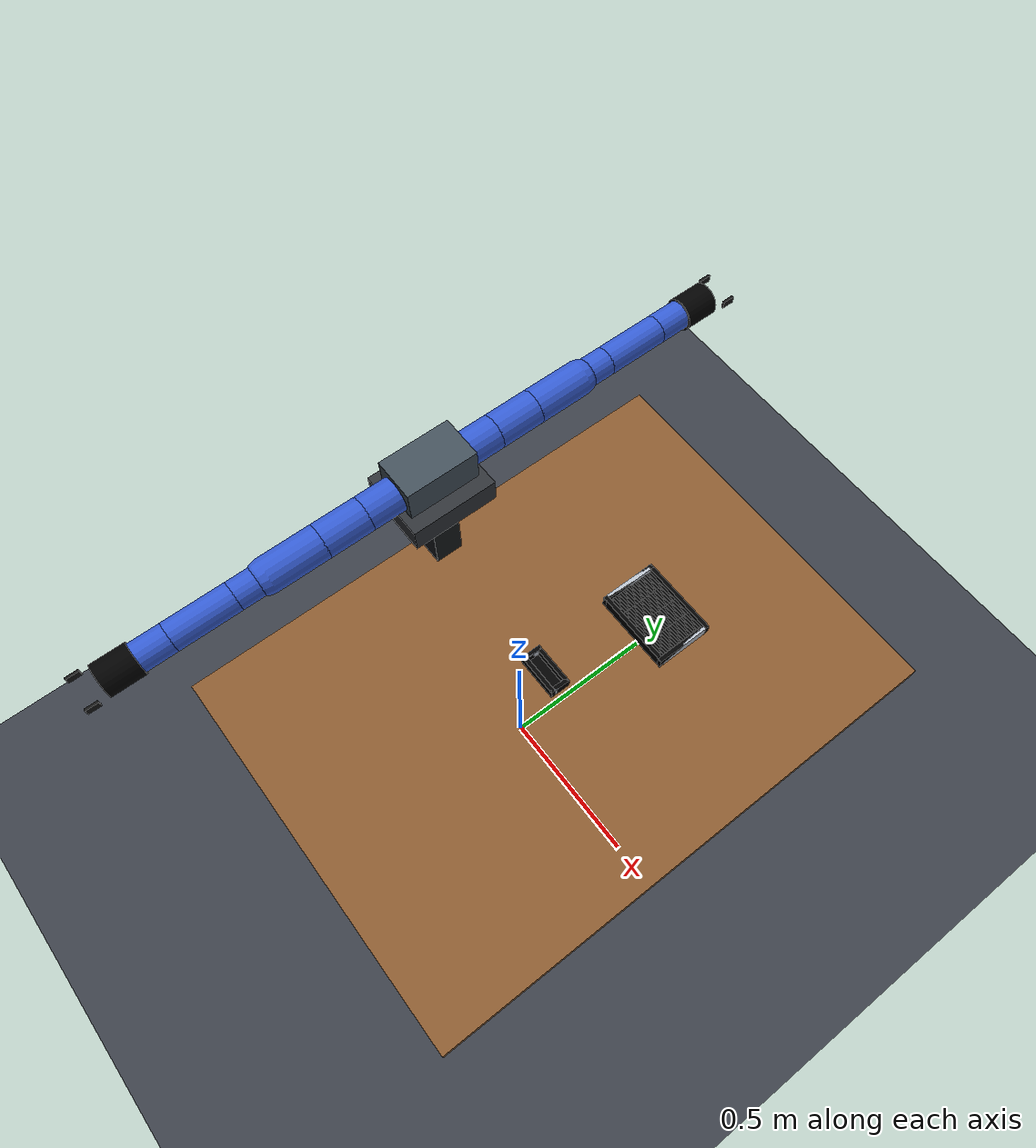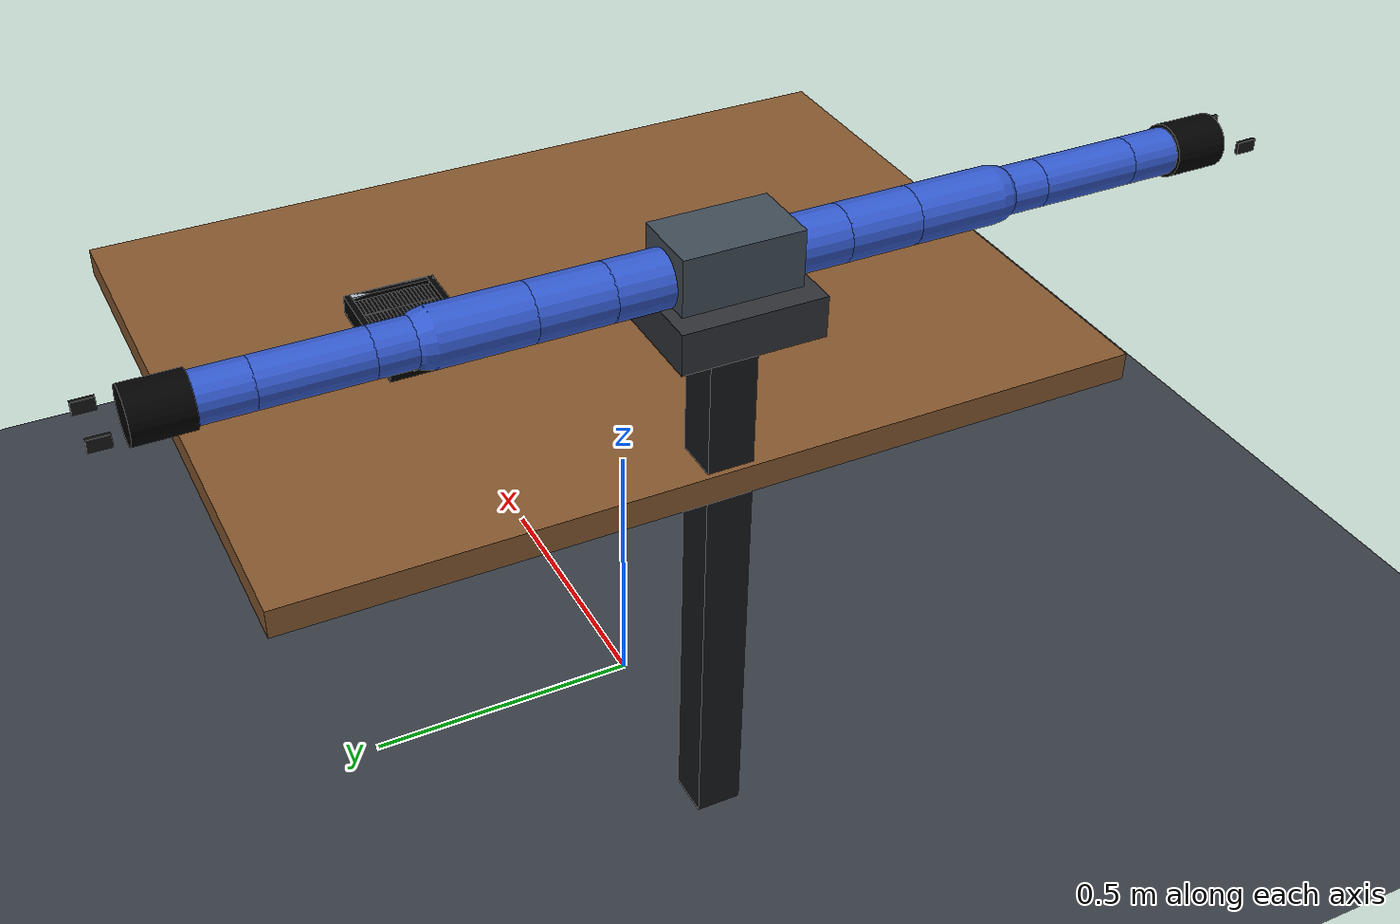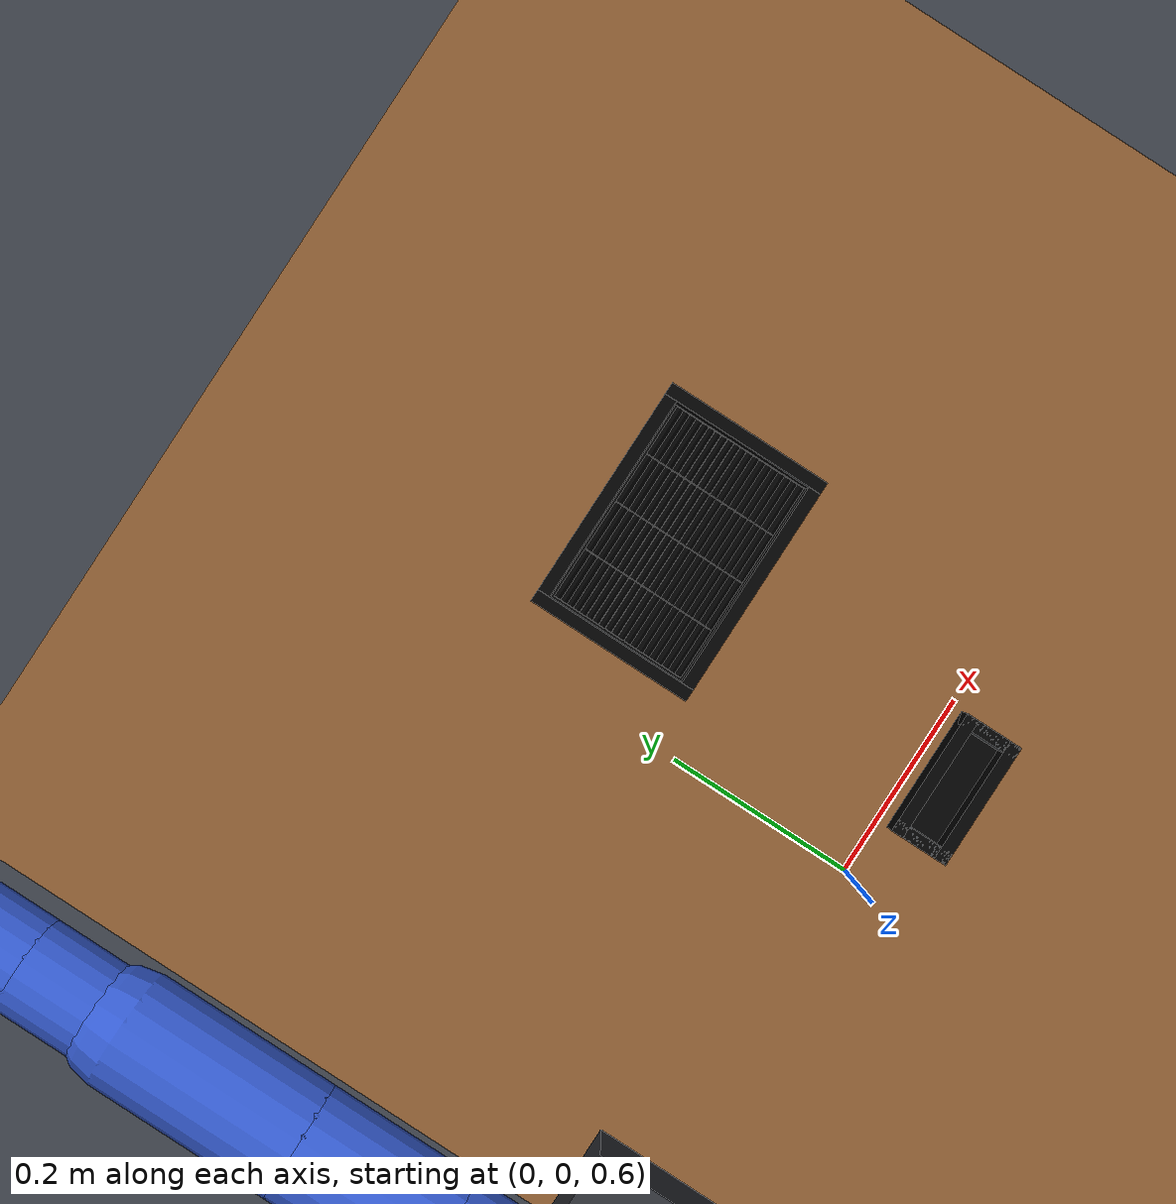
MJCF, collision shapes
<mujoco model="a3_dual_arm_cookie_transfer"><compiler angle="radian" autolimits="true" balanceinertia="true" meshdir="../assets/a3/meshes" /><option timestep="0.002" gravity="0 0 -9.81" integrator="implicitfast" cone="elliptic" impratio="10" noslip_iterations="5"><flag multiccd="enable" /></option><size nconmax="400" njmax="1000" /><visual><global offwidth="256" offheight="256" /></visual><default><joint limited="true" damping="0.8" armature="0.02" /><geom solref="0.04 0.85" solimp="0.75 0.97 0.002 0.5 2" /></default><asset><texture name="sky" type="skybox" builtin="gradient" rgb1="0.75 0.82 0.9" rgb2="0.12 0.16 0.24" width="512" height="3072" /><material name="floor" rgba="0.22 0.24 0.27 1" reflectance="0.05" /><material name="table" rgba="0.52 0.34 0.18 1" /><mesh name="mesh_base_link" file="base_link.STL" /><mesh name="mesh_L_SHOULDER_P_S" file="L_SHOULDER_P_S.STL" /><mesh name="mesh_L_SHOULDER_R_S" file="L_SHOULDER_R_S.STL" /><mesh name="mesh_L_SHOULDER_Y_S" file="L_SHOULDER_Y_S.STL" /><mesh name="mesh_L_ELBOW_P_S" file="L_ELBOW_P_S.STL" /><mesh name="mesh_L_WRIST_R_S" file="L_WRIST_R_S.STL" /><mesh name="mesh_L_WRIST_P_S" file="L_WRIST_P_S.STL" /><mesh name="mesh_L_WRIST_Y_S" file="L_WRIST_Y_S.STL" /><mesh name="mesh_R_SHOULDER_P_S" file="R_SHOULDER_P_S.STL" /><mesh name="mesh_R_SHOULDER_R_S" file="R_SHOULDER_R_S.STL" /><mesh name="mesh_R_SHOULDER_Y_S" file="R_SHOULDER_Y_S.STL" /><mesh name="mesh_R_ELBOW_P_S" file="R_ELBOW_P_S.STL" /><mesh name="mesh_R_WRIST_R_S" file="R_WRIST_R_S.STL" /><mesh name="mesh_R_WRIST_P_S" file="R_WRIST_P_S.STL" /><mesh name="mesh_R_WRIST_Y_S" file="R_WRIST_Y_S.STL" /><mesh name="robotiq_arg2f_85_base_link" file="robotiq_arg2f_85_base_link.stl" /><mesh name="robotiq_arg2f_85_outer_knuckle_vis" file="robotiq_arg2f_85_outer_knuckle_vis.stl" scale="0.001 0.001 0.001" /><mesh name="robotiq_arg2f_85_outer_finger_vis" file="robotiq_arg2f_85_outer_finger_vis.stl" scale="0.001 0.001 0.001" /><mesh name="robotiq_arg2f_85_inner_finger_vis" file="robotiq_arg2f_85_inner_finger_vis.stl" scale="0.001 0.001 0.001" /><mesh name="robotiq_arg2f_85_inner_knuckle_vis" file="robotiq_arg2f_85_inner_knuckle_vis.stl" scale="0.001 0.001 0.001" /><mesh name="cookie_collision_mesh" vertex="-0.025 -0.0006666666667 0.0125 -0.025 0.0006666666667 0.0125 -0.025 0.003166666667 0.01 -0.025 0.003166666667 -0.01 -0.025 0.0006666666667 -0.0125 -0.025 -0.0006666666667 -0.0125 -0.025 -0.003166666667 -0.01 -0.025 -0.003166666667 0.01 0.025 -0.0006666666667 0.0125 0.025 0.0006666666667 0.0125 0.025 0.003166666667 0.01 0.025 0.003166666667 -0.01 0.025 0.0006666666667 -0.0125 0.025 -0.0006666666667 -0.0125 0.025 -0.003166666667 -0.01 0.025 -0.003166666667 0.01" face="0 1 2 8 10 9 0 2 3 8 11 10 0 3 4 8 12 11 0 4 5 8 13 12 0 5 6 8 14 13 0 6 7 8 15 14 0 8 9 0 9 1 1 9 10 1 10 2 2 10 11 2 11 3 3 11 12 3 12 4 4 12 13 4 13 5 5 13 14 5 14 6 6 14 15 6 15 7 7 15 8 7 8 0" /><mesh name="cookie_visual_mesh" vertex="-0.025 -0.0006666666667 0.0125 -0.025 0.0006666666667 0.0125 -0.025 0.003166666667 0.01 -0.025 0.003166666667 -0.01 -0.025 0.0006666666667 -0.0125 -0.025 -0.0006666666667 -0.0125 -0.025 -0.003166666667 -0.01 -0.025 -0.003166666667 0.01 0.025 -0.0006666666667 0.0125 0.025 0.0006666666667 0.0125 0.025 0.003166666667 0.01 0.025 0.003166666667 -0.01 0.025 0.0006666666667 -0.0125 0.025 -0.0006666666667 -0.0125 0.025 -0.003166666667 -0.01 0.025 -0.003166666667 0.01" face="0 1 2 8 10 9 0 2 3 8 11 10 0 3 4 8 12 11 0 4 5 8 13 12 0 5 6 8 14 13 0 6 7 8 15 14 0 8 9 0 9 1 1 9 10 1 10 2 2 10 11 2 11 3 3 11 12 3 12 4 4 12 13 4 13 5 5 13 14 5 14 6 6 14 15 6 15 7 7 15 8 7 8 0" /></asset><worldbody><light pos="0.4 -0.8 2.4" dir="-0.2 0.3 -1" diffuse="0.9 0.9 0.9" /><light pos="-0.6 0.8 1.8" dir="0.2 -0.3 -1" diffuse="0.45 0.45 0.45" /><geom name="floor" type="plane" size="3 3 0.1" material="floor" contype="1" conaffinity="3" /><geom name="table_top" type="box" pos="0.15 0 0.725" size="0.55 0.75 0.025" material="table" contype="1" conaffinity="3" friction="1 0.01 0.001" /><geom name="stand_mast" type="box" pos="-0.35 0 0.55" size="0.040 0.040 0.55" rgba="0.08 0.09 0.10 1" contype="0" conaffinity="0" /><geom name="stand_bracket" type="box" pos="-0.35 0 1.03" size="0.10 0.12 0.035" rgba="0.18 0.19 0.21 1" contype="0" conaffinity="0" /><body name="workspace_target" pos="0.15 0.34 0.8"><site size="0.005" rgba="0 0 0 0" /></body><camera name="front" mode="targetbody" target="workspace_target" pos="1.3 -0.8 1.55" fovy="58" /><body name="base_link" pos="-0.35 0 1.1" gravcomp="1"><inertial pos="-2.63E-06 0 -0.00209577" mass="2.0208567" fullinertia="0.016632 0.0016659 0.016566 -9.4E-07 1.3E-07 6.8E-07" /><geom name="base_visual" type="mesh" mesh="mesh_base_link" contype="0" conaffinity="0" group="2" /><geom name="base_collision" type="box" size="0.06 0.10 0.06" rgba="0.25 0.3 0.34 0.2" contype="2" conaffinity="1" group="3" /><body name="L_SHOULDER_P_S" pos="0 0.09225 0" gravcomp="1"><joint name="L_SHOULDER_P" type="hinge" axis="0 1 0" range="-3.14 3.14" damping="0.8" armature="0.02" actuatorgravcomp="true" actuatorfrcrange="-66.0 66.0" /><inertial pos="-0.0055616 0.092768 -3.039E-05" mass="1.0048016" fullinertia="0.00095296 0.00077574 0.00099941 3.417E-05 -1.04E-06 -1.5E-07" /><geom name="L_SHOULDER_P_S_visual" type="mesh" mesh="mesh_L_SHOULDER_P_S" contype="0" conaffinity="0" group="2" /><geom name="L_SHOULDER_P_S_collision" type="capsule" fromto="0 0 0 0 0.098750 0" size="0.04600" rgba="0.2 0.35 0.8 0.12" contype="2" conaffinity="1" friction="0.8 0.01 0.001" group="3" /><body name="L_SHOULDER_R_S" pos="0 0.09875 0" gravcomp="1"><joint name="L_SHOULDER_R" type="hinge" axis="1 0 0" range="-1.57 1.57" damping="0.8" armature="0.02" actuatorgravcomp="true" actuatorfrcrange="-66.0 66.0" /><inertial pos="0.00364516 0.08784173 1.363E-05" mass="0.88590607" fullinertia="0.0022909 0.00094859 0.002429 0.00022267 5E-08 1E-07" /><geom name="L_SHOULDER_R_S_visual" type="mesh" mesh="mesh_L_SHOULDER_R_S" contype="0" conaffinity="0" group="2" /><geom name="L_SHOULDER_R_S_collision" type="capsule" fromto="0 0 0 0 0.121600 0" size="0.04600" rgba="0.2 0.35 0.8 0.12" contype="2" conaffinity="1" friction="0.8 0.01 0.001" group="3" /><body name="L_SHOULDER_Y_S" pos="0 0.1216 0" gravcomp="1"><joint name="L_SHOULDER_Y" type="hinge" axis="0 1 0" range="-3.14 3.14" damping="0.8" armature="0.02" actuatorgravcomp="true" actuatorfrcrange="-34.0 34.0" /><inertial pos="-0.00017635 0.11996932 -0.00260946" mass="0.84472136" fullinertia="0.0021111 0.00061461 0.0020422 7.03E-06 -2.25E-06 7.089E-05" /><geom name="L_SHOULDER_Y_S_visual" type="mesh" mesh="mesh_L_SHOULDER_Y_S" contype="0" conaffinity="0" group="2" /><geom name="L_SHOULDER_Y_S_collision" type="capsule" fromto="0 0 0 0 0.148400 0" size="0.04600" rgba="0.2 0.35 0.8 0.12" contype="2" conaffinity="1" friction="0.8 0.01 0.001" group="3" /><body name="L_ELBOW_P_S" pos="0 0.1484 0" gravcomp="1"><joint name="L_ELBOW_P" type="hinge" axis="0 0 1" range="-1.919 1.047" damping="0.8" armature="0.02" actuatorgravcomp="true" actuatorfrcrange="-34.0 34.0" /><inertial pos="0.00039282 0.06850127 0.00261232" mass="0.63568474" fullinertia="0.00095455 0.00051537 0.00083227 -2.61E-06 -1.54E-06 8.502E-05" /><geom name="L_ELBOW_P_S_visual" type="mesh" mesh="mesh_L_ELBOW_P_S" contype="0" conaffinity="0" group="2" /><geom name="L_ELBOW_P_S_collision" type="capsule" fromto="0 0 0 0 0.084000 0" size="0.03800" rgba="0.2 0.35 0.8 0.12" contype="2" conaffinity="1" friction="0.8 0.01 0.001" group="3" /><body name="L_WRIST_R_S" pos="0 0.084 0" gravcomp="1"><joint name="L_WRIST_R" type="hinge" axis="0 1 0" range="-3.14 3.14" damping="0.8" armature="0.02" actuatorgravcomp="true" actuatorfrcrange="-11.0 11.0" /><inertial pos="-0.00369972 0.08325037 0.03285807" mass="1.4168507" fullinertia="0.0019637 0.0011138 0.0016721 -3.631E-05 3.223E-05 -0.0002774" /><geom name="L_WRIST_R_S_visual" type="mesh" mesh="mesh_L_WRIST_R_S" contype="0" conaffinity="0" group="2" /><geom name="L_WRIST_R_S_collision" type="capsule" fromto="0 0 0 0 0.166500 0" size="0.03800" rgba="0.2 0.35 0.8 0.12" contype="2" conaffinity="1" friction="0.8 0.01 0.001" group="3" /><body name="L_WRIST_P_S" pos="0 0.1665 0" gravcomp="1"><joint name="L_WRIST_P" type="hinge" axis="0 0 1" range="-0.698 0.698" damping="0.8" armature="0.02" actuatorgravcomp="true" actuatorfrcrange="-11.0 11.0" /><inertial pos="0.01772445 0.00736871 -0.00124289" mass="0.44265407" fullinertia="0.000204 0.00028095 0.0001373 -2.378E-05 7.576E-05 3.516E-05" /><geom name="L_WRIST_P_S_visual" type="mesh" mesh="mesh_L_WRIST_P_S" contype="0" conaffinity="0" group="2" /><geom name="L_WRIST_P_S_collision" type="capsule" fromto="0 0 0 0 0.081500 0" size="0.03800" rgba="0.2 0.35 0.8 0.12" contype="2" conaffinity="1" friction="0.8 0.01 0.001" group="3" /><body name="L_WRIST_Y_S" pos="0 0 0" gravcomp="1"><joint name="L_WRIST_Y" type="hinge" axis="1 0 0" range="-1.57 1.3" damping="0.8" armature="0.02" actuatorgravcomp="true" actuatorfrcrange="-11.0 11.0" /><inertial pos="0.00299754 0.0321465 0" mass="0.18887912" fullinertia="0.00021861 0.00029978 0.00047023 2.78E-05 0 0" /><geom name="L_WRIST_Y_S_visual" type="mesh" mesh="mesh_L_WRIST_Y_S" contype="0" conaffinity="0" group="2" /><geom name="L_WRIST_Y_S_collision" type="capsule" fromto="0 0 0 0 0.081500 0" size="0.03800" rgba="0.2 0.35 0.8 0.12" contype="2" conaffinity="1" friction="0.8 0.01 0.001" group="3" /><body name="L_flange" pos="0 0.081500 0" gravcomp="1"><geom name="L_flange_geom" type="cylinder" size="0.035 0.018" euler="1.5707963268 0 0" rgba="0.25 0.25 0.28 1" contype="2" conaffinity="1" /><site name="L_eef" pos="0 0.145000 0" size="0.008" rgba="0 0 0 0" /><site name="L_wrist_ft" pos="0 0 0" size="0.012" rgba="0 0 0 0" /><body name="L_wrist_camera_target" pos="0 0.15 0" gravcomp="1"><site size="0.003" rgba="0 0 0 0" /></body><camera name="left_wrist" pos="0 0.045 0.085" mode="fixed" xyaxes="1 0 0 -0 0.6291982287 0.7772448707" fovy="70" /><body name="L_robotiq_2f85" xyaxes="0 0 1.0 1 0 0" gravcomp="1"><geom name="L_2f85_base_visual" type="mesh" mesh="robotiq_arg2f_85_base_link" rgba="0.10 0.10 0.11 1" contype="0" conaffinity="0" group="2" /><geom name="L_2f85_base_collision" type="cylinder" pos="0 0 0.045" size="0.043 0.045" rgba="0 0 0 0" contype="2" conaffinity="1" group="3" /><body name="L_finger_inner" pos="0 -0.0326011 0.054904" gravcomp="1"><joint name="L_finger_inner_joint" type="slide" axis="0 1.0 0" range="0 0.0425" damping="2" armature="0.005" actuatorgravcomp="true" actuatorfrcrange="-40 40" /><body quat="0 0 0 1" gravcomp="1"><geom type="mesh" mesh="robotiq_arg2f_85_outer_knuckle_vis" rgba="0.78 0.81 0.92 1" contype="0" conaffinity="0" group="2" /><geom type="mesh" pos="0 0.0315 -0.0041" mesh="robotiq_arg2f_85_outer_finger_vis" rgba="0.10 0.10 0.11 1" contype="0" conaffinity="0" group="2" /><body pos="0 0.0376 0.043" gravcomp="1"><geom type="mesh" mesh="robotiq_arg2f_85_inner_finger_vis" rgba="0.10 0.10 0.11 1" contype="0" conaffinity="0" group="2" /><geom name="L_finger_inner_geom" type="box" pos="0 -0.0245203 0.03242" size="0.010 0.00317500 0.01675" rgba="0.08 0.08 0.08 1" contype="2" conaffinity="1" friction="3.0 0.02 0.002" condim="4" group="3" /><geom name="L_finger_inner_pad_visual" type="box" pos="0 -0.0245203 0.03242" size="0.010 0.00317500 0.01675" rgba="0.08 0.08 0.08 1" contype="0" conaffinity="0" group="2" /><site name="L_finger_inner_touch" type="box" pos="0 -0.0245203 0.03242" size="0.0105 0.00350000 0.017" rgba="0 0 0 0" /></body></body></body><body name="L_finger_outer" pos="0 0.0326011 0.054904" gravcomp="1"><joint name="L_finger_outer_joint" type="slide" axis="0 -1.0 0" range="0 0.0425" damping="2" armature="0.005" actuatorgravcomp="true" actuatorfrcrange="-40 40" /><body quat="1 0 0 0" gravcomp="1"><geom type="mesh" mesh="robotiq_arg2f_85_outer_knuckle_vis" rgba="0.78 0.81 0.92 1" contype="0" conaffinity="0" group="2" /><geom type="mesh" pos="0 0.0315 -0.0041" mesh="robotiq_arg2f_85_outer_finger_vis" rgba="0.10 0.10 0.11 1" contype="0" conaffinity="0" group="2" /><body pos="0 0.0376 0.043" gravcomp="1"><geom type="mesh" mesh="robotiq_arg2f_85_inner_finger_vis" rgba="0.10 0.10 0.11 1" contype="0" conaffinity="0" group="2" /><geom name="L_finger_outer_geom" type="box" pos="0 -0.0245203 0.03242" size="0.010 0.00317500 0.01675" rgba="0.08 0.08 0.08 1" contype="2" conaffinity="1" friction="3.0 0.02 0.002" condim="4" group="3" /><geom name="L_finger_outer_pad_visual" type="box" pos="0 -0.0245203 0.03242" size="0.010 0.00317500 0.01675" rgba="0.08 0.08 0.08 1" contype="0" conaffinity="0" group="2" /><site name="L_finger_outer_touch" type="box" pos="0 -0.0245203 0.03242" size="0.0105 0.00350000 0.017" rgba="0 0 0 0" /></body></body></body><body name="L_2f85_inner_inner_knuckle" pos="0 -0.0127 0.06142" quat="0 0 0 1" gravcomp="1"><geom type="mesh" mesh="robotiq_arg2f_85_inner_knuckle_vis" rgba="0.10 0.10 0.11 1" contype="0" conaffinity="0" group="2" /></body><body name="L_2f85_outer_inner_knuckle" pos="0 0.0127 0.06142" quat="1 0 0 0" gravcomp="1"><geom type="mesh" mesh="robotiq_arg2f_85_inner_knuckle_vis" rgba="0.10 0.10 0.11 1" contype="0" conaffinity="0" group="2" /></body></body></body></body></body></body></body></body></body></body><body name="R_SHOULDER_P_S" pos="0 -0.09225 0" gravcomp="1"><joint name="R_SHOULDER_P" type="hinge" axis="0 -1 0" range="-3.14 3.14" damping="0.8" armature="0.02" actuatorgravcomp="true" actuatorfrcrange="-66.0 66.0" /><inertial pos="-0.00556155 -0.09307731 -3.298E-05" mass="1.0048006" fullinertia="0.00095658 0.00077575 0.001003 -4.264E-05 -1.11E-06 -5.7E-07" /><geom name="R_SHOULDER_P_S_visual" type="mesh" mesh="mesh_R_SHOULDER_P_S" contype="0" conaffinity="0" group="2" /><geom name="R_SHOULDER_P_S_collision" type="capsule" fromto="0 0 0 0 -0.098750 0" size="0.04600" rgba="0.2 0.35 0.8 0.12" contype="2" conaffinity="1" friction="0.8 0.01 0.001" group="3" /><body name="R_SHOULDER_R_S" pos="0 -0.09875 0" gravcomp="1"><joint name="R_SHOULDER_R" type="hinge" axis="1 0 0" range="-1.57 1.57" damping="0.8" armature="0.02" actuatorgravcomp="true" actuatorfrcrange="-66.0 66.0" /><inertial pos="0.00365637 -0.08782222 -1.737E-05" mass="0.88629517" fullinertia="0.0022916 0.0009488 0.00243 -0.00022323 -1.3E-07 1E-07" /><geom name="R_SHOULDER_R_S_visual" type="mesh" mesh="mesh_R_SHOULDER_R_S" contype="0" conaffinity="0" group="2" /><geom name="R_SHOULDER_R_S_collision" type="capsule" fromto="0 0 0 0 -0.121600 0" size="0.04600" rgba="0.2 0.35 0.8 0.12" contype="2" conaffinity="1" friction="0.8 0.01 0.001" group="3" /><body name="R_SHOULDER_Y_S" pos="0 -0.1216 0" gravcomp="1"><joint name="R_SHOULDER_Y" type="hinge" axis="0 -1 0" range="-3.14 3.14" damping="0.8" armature="0.02" actuatorgravcomp="true" actuatorfrcrange="-34.0 34.0" /><inertial pos="-3.68E-05 -0.12004858 -0.00260996" mass="0.84468732" fullinertia="0.0021144 0.00061488 0.002046 -3.72E-06 6.5E-07 -7.255E-05" /><geom name="R_SHOULDER_Y_S_visual" type="mesh" mesh="mesh_R_SHOULDER_Y_S" contype="0" conaffinity="0" group="2" /><geom name="R_SHOULDER_Y_S_collision" type="capsule" fromto="0 0 0 0 -0.148400 0" size="0.04600" rgba="0.2 0.35 0.8 0.12" contype="2" conaffinity="1" friction="0.8 0.01 0.001" group="3" /><body name="R_ELBOW_P_S" pos="0 -0.1484 0" gravcomp="1"><joint name="R_ELBOW_P" type="hinge" axis="0 0 1" range="-1.047 1.919" damping="0.8" armature="0.02" actuatorgravcomp="true" actuatorfrcrange="-34.0 34.0" /><inertial pos="0.00039222 -0.06852601 0.00259435" mass="0.63528252" fullinertia="0.00095363 0.00051505 0.00083163 2.63E-06 -1.57E-06 -8.458E-05" /><geom name="R_ELBOW_P_S_visual" type="mesh" mesh="mesh_R_ELBOW_P_S" contype="0" conaffinity="0" group="2" /><geom name="R_ELBOW_P_S_collision" type="capsule" fromto="0 0 0 0 -0.084000 0" size="0.03800" rgba="0.2 0.35 0.8 0.12" contype="2" conaffinity="1" friction="0.8 0.01 0.001" group="3" /><body name="R_WRIST_R_S" pos="0 -0.084 0" gravcomp="1"><joint name="R_WRIST_R" type="hinge" axis="0 -1 0" range="-3.14 3.14" damping="0.8" armature="0.02" actuatorgravcomp="true" actuatorfrcrange="-11.0 11.0" /><inertial pos="-0.00014106 -0.07968768 0.03279023" mass="1.4168568" fullinertia="0.0020843 0.0010512 0.0017366 5.63E-06 -1.724E-05 0.00022396" /><geom name="R_WRIST_R_S_visual" type="mesh" mesh="mesh_R_WRIST_R_S" contype="0" conaffinity="0" group="2" /><geom name="R_WRIST_R_S_collision" type="capsule" fromto="0 0 0 0 -0.166500 0" size="0.03800" rgba="0.2 0.35 0.8 0.12" contype="2" conaffinity="1" friction="0.8 0.01 0.001" group="3" /><body name="R_WRIST_P_S" pos="0 -0.1665 0" gravcomp="1"><joint name="R_WRIST_P" type="hinge" axis="0 0 1" range="-0.698 0.698" damping="0.8" armature="0.02" actuatorgravcomp="true" actuatorfrcrange="-11.0 11.0" /><inertial pos="0.01772445 -0.010905 0.00818421" mass="0.44265407" fullinertia="0.00014642 0.00020883 0.00015186 3.683E-05 4.164E-05 -2.971E-05" /><geom name="R_WRIST_P_S_visual" type="mesh" mesh="mesh_R_WRIST_P_S" contype="0" conaffinity="0" group="2" /><geom name="R_WRIST_P_S_collision" type="capsule" fromto="0 0 0 0 -0.081500 0" size="0.03800" rgba="0.2 0.35 0.8 0.12" contype="2" conaffinity="1" friction="0.8 0.01 0.001" group="3" /><body name="R_WRIST_Y_S" pos="0 0 0" gravcomp="1"><joint name="R_WRIST_Y" type="hinge" axis="1 0 0" range="-1.3 1.57" damping="0.8" armature="0.02" actuatorgravcomp="true" actuatorfrcrange="-11.0 11.0" /><inertial pos="0.00299762 -0.03214653 0" mass="0.18887729" fullinertia="0.0002186 0.00029978 0.00047022 -2.781E-05 0 0" /><geom name="R_WRIST_Y_S_visual" type="mesh" mesh="mesh_R_WRIST_Y_S" contype="0" conaffinity="0" group="2" /><geom name="R_WRIST_Y_S_collision" type="capsule" fromto="0 0 0 0 -0.081500 0" size="0.03800" rgba="0.2 0.35 0.8 0.12" contype="2" conaffinity="1" friction="0.8 0.01 0.001" group="3" /><body name="R_flange" pos="0 -0.081500 0" gravcomp="1"><geom name="R_flange_geom" type="cylinder" size="0.035 0.018" euler="1.5707963268 0 0" rgba="0.25 0.25 0.28 1" contype="2" conaffinity="1" /><site name="R_eef" pos="0 -0.145000 0" size="0.008" rgba="0 0 0 0" /><site name="R_wrist_ft" pos="0 0 0" size="0.012" rgba="0 0 0 0" /><body name="R_wrist_camera_target" pos="0 -0.15 0" gravcomp="1"><site size="0.003" rgba="0 0 0 0" /></body><camera name="right_wrist" pos="0 -0.045 0.085" mode="fixed" xyaxes="-1 0 0 0 -0.6291982287 0.7772448707" fovy="70" /><body name="R_robotiq_2f85" xyaxes="0 0 -1.0 1 0 0" gravcomp="1"><geom name="R_2f85_base_visual" type="mesh" mesh="robotiq_arg2f_85_base_link" rgba="0.10 0.10 0.11 1" contype="0" conaffinity="0" group="2" /><geom name="R_2f85_base_collision" type="cylinder" pos="0 0 0.045" size="0.043 0.045" rgba="0 0 0 0" contype="2" conaffinity="1" group="3" /><body name="R_finger_inner" pos="0 -0.0326011 0.054904" gravcomp="1"><joint name="R_finger_inner_joint" type="slide" axis="0 1.0 0" range="0 0.0425" damping="2" armature="0.005" actuatorgravcomp="true" actuatorfrcrange="-40 40" /><body quat="0 0 0 1" gravcomp="1"><geom type="mesh" mesh="robotiq_arg2f_85_outer_knuckle_vis" rgba="0.78 0.81 0.92 1" contype="0" conaffinity="0" group="2" /><geom type="mesh" pos="0 0.0315 -0.0041" mesh="robotiq_arg2f_85_outer_finger_vis" rgba="0.10 0.10 0.11 1" contype="0" conaffinity="0" group="2" /><body pos="0 0.0376 0.043" gravcomp="1"><geom type="mesh" mesh="robotiq_arg2f_85_inner_finger_vis" rgba="0.10 0.10 0.11 1" contype="0" conaffinity="0" group="2" /><geom name="R_finger_inner_geom" type="box" pos="0 -0.0245203 0.03242" size="0.010 0.00317500 0.01675" rgba="0.08 0.08 0.08 1" contype="2" conaffinity="1" friction="3.0 0.02 0.002" condim="4" group="3" /><geom name="R_finger_inner_pad_visual" type="box" pos="0 -0.0245203 0.03242" size="0.010 0.00317500 0.01675" rgba="0.08 0.08 0.08 1" contype="0" conaffinity="0" group="2" /><site name="R_finger_inner_touch" type="box" pos="0 -0.0245203 0.03242" size="0.0105 0.00350000 0.017" rgba="0 0 0 0" /></body></body></body><body name="R_finger_outer" pos="0 0.0326011 0.054904" gravcomp="1"><joint name="R_finger_outer_joint" type="slide" axis="0 -1.0 0" range="0 0.0425" damping="2" armature="0.005" actuatorgravcomp="true" actuatorfrcrange="-40 40" /><body quat="1 0 0 0" gravcomp="1"><geom type="mesh" mesh="robotiq_arg2f_85_outer_knuckle_vis" rgba="0.78 0.81 0.92 1" contype="0" conaffinity="0" group="2" /><geom type="mesh" pos="0 0.0315 -0.0041" mesh="robotiq_arg2f_85_outer_finger_vis" rgba="0.10 0.10 0.11 1" contype="0" conaffinity="0" group="2" /><body pos="0 0.0376 0.043" gravcomp="1"><geom type="mesh" mesh="robotiq_arg2f_85_inner_finger_vis" rgba="0.10 0.10 0.11 1" contype="0" conaffinity="0" group="2" /><geom name="R_finger_outer_geom" type="box" pos="0 -0.0245203 0.03242" size="0.010 0.00317500 0.01675" rgba="0.08 0.08 0.08 1" contype="2" conaffinity="1" friction="3.0 0.02 0.002" condim="4" group="3" /><geom name="R_finger_outer_pad_visual" type="box" pos="0 -0.0245203 0.03242" size="0.010 0.00317500 0.01675" rgba="0.08 0.08 0.08 1" contype="0" conaffinity="0" group="2" /><site name="R_finger_outer_touch" type="box" pos="0 -0.0245203 0.03242" size="0.0105 0.00350000 0.017" rgba="0 0 0 0" /></body></body></body><body name="R_2f85_inner_inner_knuckle" pos="0 -0.0127 0.06142" quat="0 0 0 1" gravcomp="1"><geom type="mesh" mesh="robotiq_arg2f_85_inner_knuckle_vis" rgba="0.10 0.10 0.11 1" contype="0" conaffinity="0" group="2" /></body><body name="R_2f85_outer_inner_knuckle" pos="0 0.0127 0.06142" quat="1 0 0 0" gravcomp="1"><geom type="mesh" mesh="robotiq_arg2f_85_inner_knuckle_vis" rgba="0.10 0.10 0.11 1" contype="0" conaffinity="0" group="2" /></body></body></body></body></body></body></body></body></body></body></body><body name="source_bin" pos="0.175 0.315 0"><geom name="source_bin_floor" type="box" pos="0.0 0.0 0.753" size="0.1096 0.07613333333333333 0.003" rgba="0 0 0 0" contype="1" conaffinity="3" friction="1.2 0.02 0.001" group="3" /><geom name="source_bin_floor_visual" type="box" pos="0.0 0.0 0.753" size="0.1096 0.07613333333333333 0.003" rgba="0.70 0.73 0.77 1" contype="0" conaffinity="0" group="2" /><geom name="source_bin_front_wall" type="box" pos="0.1096 0.0 0.768" size="0.006 0.08213333333333334 0.018" rgba="0 0 0 0" contype="1" conaffinity="3" friction="1.2 0.02 0.001" group="3" /><geom name="source_bin_back_wall" type="box" pos="-0.1096 0.0 0.768" size="0.006 0.08213333333333334 0.018" rgba="0 0 0 0" contype="1" conaffinity="3" friction="1.2 0.02 0.001" group="3" /><geom name="source_bin_left_wall" type="box" pos="0.0 0.07613333333333333 0.768" size="0.11560000000000001 0.006 0.018" rgba="0 0 0 0" contype="1" conaffinity="3" friction="1.2 0.02 0.001" group="3" /><geom name="source_bin_right_wall" type="box" pos="0.0 -0.07613333333333333 0.768" size="0.11560000000000001 0.006 0.018" rgba="0 0 0 0" contype="1" conaffinity="3" friction="1.2 0.02 0.001" group="3" /><geom name="source_bin_front_wall_visual" type="box" pos="0.1096 0.0 0.768" size="0.006 0.07013333333333333 0.018" rgba="0.70 0.73 0.77 1" contype="0" conaffinity="0" group="2" /><geom name="source_bin_back_wall_visual" type="box" pos="-0.1096 0.0 0.768" size="0.006 0.07013333333333333 0.018" rgba="0.70 0.73 0.77 1" contype="0" conaffinity="0" group="2" /><geom name="source_bin_left_wall_visual" type="box" pos="0.0 0.07613333333333333 0.768" size="0.11560000000000001 0.006 0.018" rgba="0.70 0.73 0.77 1" contype="0" conaffinity="0" group="2" /><geom name="source_bin_right_wall_visual" type="box" pos="0.0 -0.07613333333333333 0.768" size="0.11560000000000001 0.006 0.018" rgba="0.70 0.73 0.77 1" contype="0" conaffinity="0" group="2" /></body><body name="target_bin" pos="0.1246 -0.01156666667 0.753"><freejoint name="target_bin_free" /><inertial pos="0 0 0.01" mass="0.10" diaginertia="0.0002 0.0002 0.0003" /><geom name="target_bin_floor" type="box" pos="0.0 0.0 0.003" size="0.0562 0.02263333333333333 0.003" rgba="0 0 0 0" contype="1" conaffinity="3" friction="1.2 0.02 0.001" group="3" /><geom name="target_bin_floor_visual" type="box" pos="0.0 0.0 0.003" size="0.0562 0.02263333333333333 0.003" rgba="0.70 0.73 0.77 1" contype="0" conaffinity="0" group="2" /><geom name="target_bin_front_wall" type="box" pos="0.0562 0.0 0.0155" size="0.006 0.02863333333333333 0.0155" rgba="0 0 0 0" contype="1" conaffinity="3" friction="1.2 0.02 0.001" group="3" /><geom name="target_bin_back_wall" type="box" pos="-0.0562 0.0 0.0155" size="0.006 0.02863333333333333 0.0155" rgba="0 0 0 0" contype="1" conaffinity="3" friction="1.2 0.02 0.001" group="3" /><geom name="target_bin_left_wall" type="box" pos="0.0 0.02263333333333333 0.0155" size="0.0622 0.006 0.0155" rgba="0 0 0 0" contype="1" conaffinity="3" friction="1.2 0.02 0.001" group="3" /><geom name="target_bin_right_wall" type="box" pos="0.0 -0.02263333333333333 0.0155" size="0.0622 0.006 0.0155" rgba="0 0 0 0" contype="1" conaffinity="3" friction="1.2 0.02 0.001" group="3" /><geom name="target_bin_front_wall_visual" type="box" pos="0.0562 0.0 0.0155" size="0.006 0.016633333333333333 0.0155" rgba="0.70 0.73 0.77 1" contype="0" conaffinity="0" group="2" /><geom name="target_bin_back_wall_visual" type="box" pos="-0.0562 0.0 0.0155" size="0.006 0.016633333333333333 0.0155" rgba="0.70 0.73 0.77 1" contype="0" conaffinity="0" group="2" /><geom name="target_bin_left_wall_visual" type="box" pos="0.0 0.02263333333333333 0.0155" size="0.0622 0.006 0.0155" rgba="0.70 0.73 0.77 1" contype="0" conaffinity="0" group="2" /><geom name="target_bin_right_wall_visual" type="box" pos="0.0 -0.02263333333333333 0.0155" size="0.0622 0.006 0.0155" rgba="0.70 0.73 0.77 1" contype="0" conaffinity="0" group="2" /></body><body name="cookie_0" pos="0.09939999999999999 0.25103333333333333 0.7685"><freejoint name="cookie_0_free" /><geom name="cookie_0_geom" type="mesh" mesh="cookie_collision_mesh" mass="0.005833333333" rgba="0 0 0 0" contype="1" conaffinity="3" friction="2 0.03 0.002" group="3" priority="1" solref="0.01 1" solimp="0.9 0.95 0.001 0.5 2" condim="6" /><geom name="cookie_0_visual" type="mesh" mesh="cookie_visual_mesh" mass="0.0001" rgba="1.0 0.78 0.20 1" contype="0" conaffinity="0" group="2" /></body><body name="cookie_1" pos="0.09939999999999999 0.2577666666666667 0.7685"><freejoint name="cookie_1_free" /><geom name="cookie_1_geom" type="mesh" mesh="cookie_collision_mesh" mass="0.005833333333" rgba="0 0 0 0" contype="1" conaffinity="3" friction="2 0.03 0.002" group="3" priority="1" solref="0.01 1" solimp="0.9 0.95 0.001 0.5 2" condim="6" /><geom name="cookie_1_visual" type="mesh" mesh="cookie_visual_mesh" mass="0.0001" rgba="0.88 0.50 0.04 1" contype="0" conaffinity="0" group="2" /></body><body name="cookie_2" pos="0.09939999999999999 0.2645 0.7685"><freejoint name="cookie_2_free" /><geom name="cookie_2_geom" type="mesh" mesh="cookie_collision_mesh" mass="0.005833333333" rgba="0 0 0 0" contype="1" conaffinity="3" friction="2 0.03 0.002" group="3" priority="1" solref="0.01 1" solimp="0.9 0.95 0.001 0.5 2" condim="6" /><geom name="cookie_2_visual" type="mesh" mesh="cookie_visual_mesh" mass="0.0001" rgba="1.0 0.78 0.20 1" contype="0" conaffinity="0" group="2" /></body><body name="cookie_3" pos="0.09939999999999999 0.2712333333333333 0.7685"><freejoint name="cookie_3_free" /><geom name="cookie_3_geom" type="mesh" mesh="cookie_collision_mesh" mass="0.005833333333" rgba="0 0 0 0" contype="1" conaffinity="3" friction="2 0.03 0.002" group="3" priority="1" solref="0.01 1" solimp="0.9 0.95 0.001 0.5 2" condim="6" /><geom name="cookie_3_visual" type="mesh" mesh="cookie_visual_mesh" mass="0.0001" rgba="0.88 0.50 0.04 1" contype="0" conaffinity="0" group="2" /></body><body name="cookie_4" pos="0.09939999999999999 0.2779666666666667 0.7685"><freejoint name="cookie_4_free" /><geom name="cookie_4_geom" type="mesh" mesh="cookie_collision_mesh" mass="0.005833333333" rgba="0 0 0 0" contype="1" conaffinity="3" friction="2 0.03 0.002" group="3" priority="1" solref="0.01 1" solimp="0.9 0.95 0.001 0.5 2" condim="6" /><geom name="cookie_4_visual" type="mesh" mesh="cookie_visual_mesh" mass="0.0001" rgba="1.0 0.78 0.20 1" contype="0" conaffinity="0" group="2" /></body><body name="cookie_5" pos="0.09939999999999999 0.2847 0.7685"><freejoint name="cookie_5_free" /><geom name="cookie_5_geom" type="mesh" mesh="cookie_collision_mesh" mass="0.005833333333" rgba="0 0 0 0" contype="1" conaffinity="3" friction="2 0.03 0.002" group="3" priority="1" solref="0.01 1" solimp="0.9 0.95 0.001 0.5 2" condim="6" /><geom name="cookie_5_visual" type="mesh" mesh="cookie_visual_mesh" mass="0.0001" rgba="0.88 0.50 0.04 1" contype="0" conaffinity="0" group="2" /></body><body name="cookie_6" pos="0.09939999999999999 0.2914333333333333 0.7685"><freejoint name="cookie_6_free" /><geom name="cookie_6_geom" type="mesh" mesh="cookie_collision_mesh" mass="0.005833333333" rgba="0 0 0 0" contype="1" conaffinity="3" friction="2 0.03 0.002" group="3" priority="1" solref="0.01 1" solimp="0.9 0.95 0.001 0.5 2" condim="6" /><geom name="cookie_6_visual" type="mesh" mesh="cookie_visual_mesh" mass="0.0001" rgba="1.0 0.78 0.20 1" contype="0" conaffinity="0" group="2" /></body><body name="cookie_7" pos="0.09939999999999999 0.2981666666666667 0.7685"><freejoint name="cookie_7_free" /><geom name="cookie_7_geom" type="mesh" mesh="cookie_collision_mesh" mass="0.005833333333" rgba="0 0 0 0" contype="1" conaffinity="3" friction="2 0.03 0.002" group="3" priority="1" solref="0.01 1" solimp="0.9 0.95 0.001 0.5 2" condim="6" /><geom name="cookie_7_visual" type="mesh" mesh="cookie_visual_mesh" mass="0.0001" rgba="0.88 0.50 0.04 1" contype="0" conaffinity="0" group="2" /></body><body name="cookie_8" pos="0.09939999999999999 0.3049 0.7685"><freejoint name="cookie_8_free" /><geom name="cookie_8_geom" type="mesh" mesh="cookie_collision_mesh" mass="0.005833333333" rgba="0 0 0 0" contype="1" conaffinity="3" friction="2 0.03 0.002" group="3" priority="1" solref="0.01 1" solimp="0.9 0.95 0.001 0.5 2" condim="6" /><geom name="cookie_8_visual" type="mesh" mesh="cookie_visual_mesh" mass="0.0001" rgba="1.0 0.78 0.20 1" contype="0" conaffinity="0" group="2" /></body><body name="cookie_9" pos="0.09939999999999999 0.3116333333333333 0.7685"><freejoint name="cookie_9_free" /><geom name="cookie_9_geom" type="mesh" mesh="cookie_collision_mesh" mass="0.005833333333" rgba="0 0 0 0" contype="1" conaffinity="3" friction="2 0.03 0.002" group="3" priority="1" solref="0.01 1" solimp="0.9 0.95 0.001 0.5 2" condim="6" /><geom name="cookie_9_visual" type="mesh" mesh="cookie_visual_mesh" mass="0.0001" rgba="0.88 0.50 0.04 1" contype="0" conaffinity="0" group="2" /></body><body name="cookie_10" pos="0.09939999999999999 0.3183666666666667 0.7685"><freejoint name="cookie_10_free" /><geom name="cookie_10_geom" type="mesh" mesh="cookie_collision_mesh" mass="0.005833333333" rgba="0 0 0 0" contype="1" conaffinity="3" friction="2 0.03 0.002" group="3" priority="1" solref="0.01 1" solimp="0.9 0.95 0.001 0.5 2" condim="6" /><geom name="cookie_10_visual" type="mesh" mesh="cookie_visual_mesh" mass="0.0001" rgba="1.0 0.78 0.20 1" contype="0" conaffinity="0" group="2" /></body><body name="cookie_11" pos="0.09939999999999999 0.3251 0.7685"><freejoint name="cookie_11_free" /><geom name="cookie_11_geom" type="mesh" mesh="cookie_collision_mesh" mass="0.005833333333" rgba="0 0 0 0" contype="1" conaffinity="3" friction="2 0.03 0.002" group="3" priority="1" solref="0.01 1" solimp="0.9 0.95 0.001 0.5 2" condim="6" /><geom name="cookie_11_visual" type="mesh" mesh="cookie_visual_mesh" mass="0.0001" rgba="0.88 0.50 0.04 1" contype="0" conaffinity="0" group="2" /></body><body name="cookie_12" pos="0.09939999999999999 0.3318333333333333 0.7685"><freejoint name="cookie_12_free" /><geom name="cookie_12_geom" type="mesh" mesh="cookie_collision_mesh" mass="0.005833333333" rgba="0 0 0 0" contype="1" conaffinity="3" friction="2 0.03 0.002" group="3" priority="1" solref="0.01 1" solimp="0.9 0.95 0.001 0.5 2" condim="6" /><geom name="cookie_12_visual" type="mesh" mesh="cookie_visual_mesh" mass="0.0001" rgba="1.0 0.78 0.20 1" contype="0" conaffinity="0" group="2" /></body><body name="cookie_13" pos="0.09939999999999999 0.3385666666666667 0.7685"><freejoint name="cookie_13_free" /><geom name="cookie_13_geom" type="mesh" mesh="cookie_collision_mesh" mass="0.005833333333" rgba="0 0 0 0" contype="1" conaffinity="3" friction="2 0.03 0.002" group="3" priority="1" solref="0.01 1" solimp="0.9 0.95 0.001 0.5 2" condim="6" /><geom name="cookie_13_visual" type="mesh" mesh="cookie_visual_mesh" mass="0.0001" rgba="0.88 0.50 0.04 1" contype="0" conaffinity="0" group="2" /></body><body name="cookie_14" pos="0.09939999999999999 0.3453 0.7685"><freejoint name="cookie_14_free" /><geom name="cookie_14_geom" type="mesh" mesh="cookie_collision_mesh" mass="0.005833333333" rgba="0 0 0 0" contype="1" conaffinity="3" friction="2 0.03 0.002" group="3" priority="1" solref="0.01 1" solimp="0.9 0.95 0.001 0.5 2" condim="6" /><geom name="cookie_14_visual" type="mesh" mesh="cookie_visual_mesh" mass="0.0001" rgba="1.0 0.78 0.20 1" contype="0" conaffinity="0" group="2" /></body><body name="cookie_15" pos="0.09939999999999999 0.3520333333333333 0.7685"><freejoint name="cookie_15_free" /><geom name="cookie_15_geom" type="mesh" mesh="cookie_collision_mesh" mass="0.005833333333" rgba="0 0 0 0" contype="1" conaffinity="3" friction="2 0.03 0.002" group="3" priority="1" solref="0.01 1" solimp="0.9 0.95 0.001 0.5 2" condim="6" /><geom name="cookie_15_visual" type="mesh" mesh="cookie_visual_mesh" mass="0.0001" rgba="0.88 0.50 0.04 1" contype="0" conaffinity="0" group="2" /></body><body name="cookie_16" pos="0.09939999999999999 0.3587666666666667 0.7685"><freejoint name="cookie_16_free" /><geom name="cookie_16_geom" type="mesh" mesh="cookie_collision_mesh" mass="0.005833333333" rgba="0 0 0 0" contype="1" conaffinity="3" friction="2 0.03 0.002" group="3" priority="1" solref="0.01 1" solimp="0.9 0.95 0.001 0.5 2" condim="6" /><geom name="cookie_16_visual" type="mesh" mesh="cookie_visual_mesh" mass="0.0001" rgba="1.0 0.78 0.20 1" contype="0" conaffinity="0" group="2" /></body><body name="cookie_17" pos="0.09939999999999999 0.3655 0.7685"><freejoint name="cookie_17_free" /><geom name="cookie_17_geom" type="mesh" mesh="cookie_collision_mesh" mass="0.005833333333" rgba="0 0 0 0" contype="1" conaffinity="3" friction="2 0.03 0.002" group="3" priority="1" solref="0.01 1" solimp="0.9 0.95 0.001 0.5 2" condim="6" /><geom name="cookie_17_visual" type="mesh" mesh="cookie_visual_mesh" mass="0.0001" rgba="0.88 0.50 0.04 1" contype="0" conaffinity="0" group="2" /></body><body name="cookie_18" pos="0.09939999999999999 0.3722333333333333 0.7685"><freejoint name="cookie_18_free" /><geom name="cookie_18_geom" type="mesh" mesh="cookie_collision_mesh" mass="0.005833333333" rgba="0 0 0 0" contype="1" conaffinity="3" friction="2 0.03 0.002" group="3" priority="1" solref="0.01 1" solimp="0.9 0.95 0.001 0.5 2" condim="6" /><geom name="cookie_18_visual" type="mesh" mesh="cookie_visual_mesh" mass="0.0001" rgba="1.0 0.78 0.20 1" contype="0" conaffinity="0" group="2" /></body><body name="cookie_19" pos="0.09939999999999999 0.3789666666666667 0.7685"><freejoint name="cookie_19_free" /><geom name="cookie_19_geom" type="mesh" mesh="cookie_collision_mesh" mass="0.005833333333" rgba="0 0 0 0" contype="1" conaffinity="3" friction="2 0.03 0.002" group="3" priority="1" solref="0.01 1" solimp="0.9 0.95 0.001 0.5 2" condim="6" /><geom name="cookie_19_visual" type="mesh" mesh="cookie_visual_mesh" mass="0.0001" rgba="0.88 0.50 0.04 1" contype="0" conaffinity="0" group="2" /></body><body name="cookie_20" pos="0.1498 0.25103333333333333 0.7685"><freejoint name="cookie_20_free" /><geom name="cookie_20_geom" type="mesh" mesh="cookie_collision_mesh" mass="0.005833333333" rgba="0 0 0 0" contype="1" conaffinity="3" friction="2 0.03 0.002" group="3" priority="1" solref="0.01 1" solimp="0.9 0.95 0.001 0.5 2" condim="6" /><geom name="cookie_20_visual" type="mesh" mesh="cookie_visual_mesh" mass="0.0001" rgba="0.88 0.50 0.04 1" contype="0" conaffinity="0" group="2" /></body><body name="cookie_21" pos="0.1498 0.2577666666666667 0.7685"><freejoint name="cookie_21_free" /><geom name="cookie_21_geom" type="mesh" mesh="cookie_collision_mesh" mass="0.005833333333" rgba="0 0 0 0" contype="1" conaffinity="3" friction="2 0.03 0.002" group="3" priority="1" solref="0.01 1" solimp="0.9 0.95 0.001 0.5 2" condim="6" /><geom name="cookie_21_visual" type="mesh" mesh="cookie_visual_mesh" mass="0.0001" rgba="1.0 0.78 0.20 1" contype="0" conaffinity="0" group="2" /></body><body name="cookie_22" pos="0.1498 0.2645 0.7685"><freejoint name="cookie_22_free" /><geom name="cookie_22_geom" type="mesh" mesh="cookie_collision_mesh" mass="0.005833333333" rgba="0 0 0 0" contype="1" conaffinity="3" friction="2 0.03 0.002" group="3" priority="1" solref="0.01 1" solimp="0.9 0.95 0.001 0.5 2" condim="6" /><geom name="cookie_22_visual" type="mesh" mesh="cookie_visual_mesh" mass="0.0001" rgba="0.88 0.50 0.04 1" contype="0" conaffinity="0" group="2" /></body><body name="cookie_23" pos="0.1498 0.2712333333333333 0.7685"><freejoint name="cookie_23_free" /><geom name="cookie_23_geom" type="mesh" mesh="cookie_collision_mesh" mass="0.005833333333" rgba="0 0 0 0" contype="1" conaffinity="3" friction="2 0.03 0.002" group="3" priority="1" solref="0.01 1" solimp="0.9 0.95 0.001 0.5 2" condim="6" /><geom name="cookie_23_visual" type="mesh" mesh="cookie_visual_mesh" mass="0.0001" rgba="1.0 0.78 0.20 1" contype="0" conaffinity="0" group="2" /></body><body name="cookie_24" pos="0.1498 0.2779666666666667 0.7685"><freejoint name="cookie_24_free" /><geom name="cookie_24_geom" type="mesh" mesh="cookie_collision_mesh" mass="0.005833333333" rgba="0 0 0 0" contype="1" conaffinity="3" friction="2 0.03 0.002" group="3" priority="1" solref="0.01 1" solimp="0.9 0.95 0.001 0.5 2" condim="6" /><geom name="cookie_24_visual" type="mesh" mesh="cookie_visual_mesh" mass="0.0001" rgba="0.88 0.50 0.04 1" contype="0" conaffinity="0" group="2" /></body><body name="cookie_25" pos="0.1498 0.2847 0.7685"><freejoint name="cookie_25_free" /><geom name="cookie_25_geom" type="mesh" mesh="cookie_collision_mesh" mass="0.005833333333" rgba="0 0 0 0" contype="1" conaffinity="3" friction="2 0.03 0.002" group="3" priority="1" solref="0.01 1" solimp="0.9 0.95 0.001 0.5 2" condim="6" /><geom name="cookie_25_visual" type="mesh" mesh="cookie_visual_mesh" mass="0.0001" rgba="1.0 0.78 0.20 1" contype="0" conaffinity="0" group="2" /></body><body name="cookie_26" pos="0.1498 0.2914333333333333 0.7685"><freejoint name="cookie_26_free" /><geom name="cookie_26_geom" type="mesh" mesh="cookie_collision_mesh" mass="0.005833333333" rgba="0 0 0 0" contype="1" conaffinity="3" friction="2 0.03 0.002" group="3" priority="1" solref="0.01 1" solimp="0.9 0.95 0.001 0.5 2" condim="6" /><geom name="cookie_26_visual" type="mesh" mesh="cookie_visual_mesh" mass="0.0001" rgba="0.88 0.50 0.04 1" contype="0" conaffinity="0" group="2" /></body><body name="cookie_27" pos="0.1498 0.2981666666666667 0.7685"><freejoint name="cookie_27_free" /><geom name="cookie_27_geom" type="mesh" mesh="cookie_collision_mesh" mass="0.005833333333" rgba="0 0 0 0" contype="1" conaffinity="3" friction="2 0.03 0.002" group="3" priority="1" solref="0.01 1" solimp="0.9 0.95 0.001 0.5 2" condim="6" /><geom name="cookie_27_visual" type="mesh" mesh="cookie_visual_mesh" mass="0.0001" rgba="1.0 0.78 0.20 1" contype="0" conaffinity="0" group="2" /></body><body name="cookie_28" pos="0.1498 0.3049 0.7685"><freejoint name="cookie_28_free" /><geom name="cookie_28_geom" type="mesh" mesh="cookie_collision_mesh" mass="0.005833333333" rgba="0 0 0 0" contype="1" conaffinity="3" friction="2 0.03 0.002" group="3" priority="1" solref="0.01 1" solimp="0.9 0.95 0.001 0.5 2" condim="6" /><geom name="cookie_28_visual" type="mesh" mesh="cookie_visual_mesh" mass="0.0001" rgba="0.88 0.50 0.04 1" contype="0" conaffinity="0" group="2" /></body><body name="cookie_29" pos="0.1498 0.3116333333333333 0.7685"><freejoint name="cookie_29_free" /><geom name="cookie_29_geom" type="mesh" mesh="cookie_collision_mesh" mass="0.005833333333" rgba="0 0 0 0" contype="1" conaffinity="3" friction="2 0.03 0.002" group="3" priority="1" solref="0.01 1" solimp="0.9 0.95 0.001 0.5 2" condim="6" /><geom name="cookie_29_visual" type="mesh" mesh="cookie_visual_mesh" mass="0.0001" rgba="1.0 0.78 0.20 1" contype="0" conaffinity="0" group="2" /></body><body name="cookie_30" pos="0.1498 0.3183666666666667 0.7685"><freejoint name="cookie_30_free" /><geom name="cookie_30_geom" type="mesh" mesh="cookie_collision_mesh" mass="0.005833333333" rgba="0 0 0 0" contype="1" conaffinity="3" friction="2 0.03 0.002" group="3" priority="1" solref="0.01 1" solimp="0.9 0.95 0.001 0.5 2" condim="6" /><geom name="cookie_30_visual" type="mesh" mesh="cookie_visual_mesh" mass="0.0001" rgba="0.88 0.50 0.04 1" contype="0" conaffinity="0" group="2" /></body><body name="cookie_31" pos="0.1498 0.3251 0.7685"><freejoint name="cookie_31_free" /><geom name="cookie_31_geom" type="mesh" mesh="cookie_collision_mesh" mass="0.005833333333" rgba="0 0 0 0" contype="1" conaffinity="3" friction="2 0.03 0.002" group="3" priority="1" solref="0.01 1" solimp="0.9 0.95 0.001 0.5 2" condim="6" /><geom name="cookie_31_visual" type="mesh" mesh="cookie_visual_mesh" mass="0.0001" rgba="1.0 0.78 0.20 1" contype="0" conaffinity="0" group="2" /></body><body name="cookie_32" pos="0.1498 0.3318333333333333 0.7685"><freejoint name="cookie_32_free" /><geom name="cookie_32_geom" type="mesh" mesh="cookie_collision_mesh" mass="0.005833333333" rgba="0 0 0 0" contype="1" conaffinity="3" friction="2 0.03 0.002" group="3" priority="1" solref="0.01 1" solimp="0.9 0.95 0.001 0.5 2" condim="6" /><geom name="cookie_32_visual" type="mesh" mesh="cookie_visual_mesh" mass="0.0001" rgba="0.88 0.50 0.04 1" contype="0" conaffinity="0" group="2" /></body><body name="cookie_33" pos="0.1498 0.3385666666666667 0.7685"><freejoint name="cookie_33_free" /><geom name="cookie_33_geom" type="mesh" mesh="cookie_collision_mesh" mass="0.005833333333" rgba="0 0 0 0" contype="1" conaffinity="3" friction="2 0.03 0.002" group="3" priority="1" solref="0.01 1" solimp="0.9 0.95 0.001 0.5 2" condim="6" /><geom name="cookie_33_visual" type="mesh" mesh="cookie_visual_mesh" mass="0.0001" rgba="1.0 0.78 0.20 1" contype="0" conaffinity="0" group="2" /></body><body name="cookie_34" pos="0.1498 0.3453 0.7685"><freejoint name="cookie_34_free" /><geom name="cookie_34_geom" type="mesh" mesh="cookie_collision_mesh" mass="0.005833333333" rgba="0 0 0 0" contype="1" conaffinity="3" friction="2 0.03 0.002" group="3" priority="1" solref="0.01 1" solimp="0.9 0.95 0.001 0.5 2" condim="6" /><geom name="cookie_34_visual" type="mesh" mesh="cookie_visual_mesh" mass="0.0001" rgba="0.88 0.50 0.04 1" contype="0" conaffinity="0" group="2" /></body><body name="cookie_35" pos="0.1498 0.3520333333333333 0.7685"><freejoint name="cookie_35_free" /><geom name="cookie_35_geom" type="mesh" mesh="cookie_collision_mesh" mass="0.005833333333" rgba="0 0 0 0" contype="1" conaffinity="3" friction="2 0.03 0.002" group="3" priority="1" solref="0.01 1" solimp="0.9 0.95 0.001 0.5 2" condim="6" /><geom name="cookie_35_visual" type="mesh" mesh="cookie_visual_mesh" mass="0.0001" rgba="1.0 0.78 0.20 1" contype="0" conaffinity="0" group="2" /></body><body name="cookie_36" pos="0.1498 0.3587666666666667 0.7685"><freejoint name="cookie_36_free" /><geom name="cookie_36_geom" type="mesh" mesh="cookie_collision_mesh" mass="0.005833333333" rgba="0 0 0 0" contype="1" conaffinity="3" friction="2 0.03 0.002" group="3" priority="1" solref="0.01 1" solimp="0.9 0.95 0.001 0.5 2" condim="6" /><geom name="cookie_36_visual" type="mesh" mesh="cookie_visual_mesh" mass="0.0001" rgba="0.88 0.50 0.04 1" contype="0" conaffinity="0" group="2" /></body><body name="cookie_37" pos="0.1498 0.3655 0.7685"><freejoint name="cookie_37_free" /><geom name="cookie_37_geom" type="mesh" mesh="cookie_collision_mesh" mass="0.005833333333" rgba="0 0 0 0" contype="1" conaffinity="3" friction="2 0.03 0.002" group="3" priority="1" solref="0.01 1" solimp="0.9 0.95 0.001 0.5 2" condim="6" /><geom name="cookie_37_visual" type="mesh" mesh="cookie_visual_mesh" mass="0.0001" rgba="1.0 0.78 0.20 1" contype="0" conaffinity="0" group="2" /></body><body name="cookie_38" pos="0.1498 0.3722333333333333 0.7685"><freejoint name="cookie_38_free" /><geom name="cookie_38_geom" type="mesh" mesh="cookie_collision_mesh" mass="0.005833333333" rgba="0 0 0 0" contype="1" conaffinity="3" friction="2 0.03 0.002" group="3" priority="1" solref="0.01 1" solimp="0.9 0.95 0.001 0.5 2" condim="6" /><geom name="cookie_38_visual" type="mesh" mesh="cookie_visual_mesh" mass="0.0001" rgba="0.88 0.50 0.04 1" contype="0" conaffinity="0" group="2" /></body><body name="cookie_39" pos="0.1498 0.3789666666666667 0.7685"><freejoint name="cookie_39_free" /><geom name="cookie_39_geom" type="mesh" mesh="cookie_collision_mesh" mass="0.005833333333" rgba="0 0 0 0" contype="1" conaffinity="3" friction="2 0.03 0.002" group="3" priority="1" solref="0.01 1" solimp="0.9 0.95 0.001 0.5 2" condim="6" /><geom name="cookie_39_visual" type="mesh" mesh="cookie_visual_mesh" mass="0.0001" rgba="1.0 0.78 0.20 1" contype="0" conaffinity="0" group="2" /></body><body name="cookie_40" pos="0.2002 0.25103333333333333 0.7685"><freejoint name="cookie_40_free" /><geom name="cookie_40_geom" type="mesh" mesh="cookie_collision_mesh" mass="0.005833333333" rgba="0 0 0 0" contype="1" conaffinity="3" friction="2 0.03 0.002" group="3" priority="1" solref="0.01 1" solimp="0.9 0.95 0.001 0.5 2" condim="6" /><geom name="cookie_40_visual" type="mesh" mesh="cookie_visual_mesh" mass="0.0001" rgba="1.0 0.78 0.20 1" contype="0" conaffinity="0" group="2" /></body><body name="cookie_41" pos="0.2002 0.2577666666666667 0.7685"><freejoint name="cookie_41_free" /><geom name="cookie_41_geom" type="mesh" mesh="cookie_collision_mesh" mass="0.005833333333" rgba="0 0 0 0" contype="1" conaffinity="3" friction="2 0.03 0.002" group="3" priority="1" solref="0.01 1" solimp="0.9 0.95 0.001 0.5 2" condim="6" /><geom name="cookie_41_visual" type="mesh" mesh="cookie_visual_mesh" mass="0.0001" rgba="0.88 0.50 0.04 1" contype="0" conaffinity="0" group="2" /></body><body name="cookie_42" pos="0.2002 0.2645 0.7685"><freejoint name="cookie_42_free" /><geom name="cookie_42_geom" type="mesh" mesh="cookie_collision_mesh" mass="0.005833333333" rgba="0 0 0 0" contype="1" conaffinity="3" friction="2 0.03 0.002" group="3" priority="1" solref="0.01 1" solimp="0.9 0.95 0.001 0.5 2" condim="6" /><geom name="cookie_42_visual" type="mesh" mesh="cookie_visual_mesh" mass="0.0001" rgba="1.0 0.78 0.20 1" contype="0" conaffinity="0" group="2" /></body><body name="cookie_43" pos="0.2002 0.2712333333333333 0.7685"><freejoint name="cookie_43_free" /><geom name="cookie_43_geom" type="mesh" mesh="cookie_collision_mesh" mass="0.005833333333" rgba="0 0 0 0" contype="1" conaffinity="3" friction="2 0.03 0.002" group="3" priority="1" solref="0.01 1" solimp="0.9 0.95 0.001 0.5 2" condim="6" /><geom name="cookie_43_visual" type="mesh" mesh="cookie_visual_mesh" mass="0.0001" rgba="0.88 0.50 0.04 1" contype="0" conaffinity="0" group="2" /></body><body name="cookie_44" pos="0.2002 0.2779666666666667 0.7685"><freejoint name="cookie_44_free" /><geom name="cookie_44_geom" type="mesh" mesh="cookie_collision_mesh" mass="0.005833333333" rgba="0 0 0 0" contype="1" conaffinity="3" friction="2 0.03 0.002" group="3" priority="1" solref="0.01 1" solimp="0.9 0.95 0.001 0.5 2" condim="6" /><geom name="cookie_44_visual" type="mesh" mesh="cookie_visual_mesh" mass="0.0001" rgba="1.0 0.78 0.20 1" contype="0" conaffinity="0" group="2" /></body><body name="cookie_45" pos="0.2002 0.2847 0.7685"><freejoint name="cookie_45_free" /><geom name="cookie_45_geom" type="mesh" mesh="cookie_collision_mesh" mass="0.005833333333" rgba="0 0 0 0" contype="1" conaffinity="3" friction="2 0.03 0.002" group="3" priority="1" solref="0.01 1" solimp="0.9 0.95 0.001 0.5 2" condim="6" /><geom name="cookie_45_visual" type="mesh" mesh="cookie_visual_mesh" mass="0.0001" rgba="0.88 0.50 0.04 1" contype="0" conaffinity="0" group="2" /></body><body name="cookie_46" pos="0.2002 0.2914333333333333 0.7685"><freejoint name="cookie_46_free" /><geom name="cookie_46_geom" type="mesh" mesh="cookie_collision_mesh" mass="0.005833333333" rgba="0 0 0 0" contype="1" conaffinity="3" friction="2 0.03 0.002" group="3" priority="1" solref="0.01 1" solimp="0.9 0.95 0.001 0.5 2" condim="6" /><geom name="cookie_46_visual" type="mesh" mesh="cookie_visual_mesh" mass="0.0001" rgba="1.0 0.78 0.20 1" contype="0" conaffinity="0" group="2" /></body><body name="cookie_47" pos="0.2002 0.2981666666666667 0.7685"><freejoint name="cookie_47_free" /><geom name="cookie_47_geom" type="mesh" mesh="cookie_collision_mesh" mass="0.005833333333" rgba="0 0 0 0" contype="1" conaffinity="3" friction="2 0.03 0.002" group="3" priority="1" solref="0.01 1" solimp="0.9 0.95 0.001 0.5 2" condim="6" /><geom name="cookie_47_visual" type="mesh" mesh="cookie_visual_mesh" mass="0.0001" rgba="0.88 0.50 0.04 1" contype="0" conaffinity="0" group="2" /></body><body name="cookie_48" pos="0.2002 0.3049 0.7685"><freejoint name="cookie_48_free" /><geom name="cookie_48_geom" type="mesh" mesh="cookie_collision_mesh" mass="0.005833333333" rgba="0 0 0 0" contype="1" conaffinity="3" friction="2 0.03 0.002" group="3" priority="1" solref="0.01 1" solimp="0.9 0.95 0.001 0.5 2" condim="6" /><geom name="cookie_48_visual" type="mesh" mesh="cookie_visual_mesh" mass="0.0001" rgba="1.0 0.78 0.20 1" contype="0" conaffinity="0" group="2" /></body><body name="cookie_49" pos="0.2002 0.3116333333333333 0.7685"><freejoint name="cookie_49_free" /><geom name="cookie_49_geom" type="mesh" mesh="cookie_collision_mesh" mass="0.005833333333" rgba="0 0 0 0" contype="1" conaffinity="3" friction="2 0.03 0.002" group="3" priority="1" solref="0.01 1" solimp="0.9 0.95 0.001 0.5 2" condim="6" /><geom name="cookie_49_visual" type="mesh" mesh="cookie_visual_mesh" mass="0.0001" rgba="0.88 0.50 0.04 1" contype="0" conaffinity="0" group="2" /></body><body name="cookie_50" pos="0.2002 0.3183666666666667 0.7685"><freejoint name="cookie_50_free" /><geom name="cookie_50_geom" type="mesh" mesh="cookie_collision_mesh" mass="0.005833333333" rgba="0 0 0 0" contype="1" conaffinity="3" friction="2 0.03 0.002" group="3" priority="1" solref="0.01 1" solimp="0.9 0.95 0.001 0.5 2" condim="6" /><geom name="cookie_50_visual" type="mesh" mesh="cookie_visual_mesh" mass="0.0001" rgba="1.0 0.78 0.20 1" contype="0" conaffinity="0" group="2" /></body><body name="cookie_51" pos="0.2002 0.3251 0.7685"><freejoint name="cookie_51_free" /><geom name="cookie_51_geom" type="mesh" mesh="cookie_collision_mesh" mass="0.005833333333" rgba="0 0 0 0" contype="1" conaffinity="3" friction="2 0.03 0.002" group="3" priority="1" solref="0.01 1" solimp="0.9 0.95 0.001 0.5 2" condim="6" /><geom name="cookie_51_visual" type="mesh" mesh="cookie_visual_mesh" mass="0.0001" rgba="0.88 0.50 0.04 1" contype="0" conaffinity="0" group="2" /></body><body name="cookie_52" pos="0.2002 0.3318333333333333 0.7685"><freejoint name="cookie_52_free" /><geom name="cookie_52_geom" type="mesh" mesh="cookie_collision_mesh" mass="0.005833333333" rgba="0 0 0 0" contype="1" conaffinity="3" friction="2 0.03 0.002" group="3" priority="1" solref="0.01 1" solimp="0.9 0.95 0.001 0.5 2" condim="6" /><geom name="cookie_52_visual" type="mesh" mesh="cookie_visual_mesh" mass="0.0001" rgba="1.0 0.78 0.20 1" contype="0" conaffinity="0" group="2" /></body><body name="cookie_53" pos="0.2002 0.3385666666666667 0.7685"><freejoint name="cookie_53_free" /><geom name="cookie_53_geom" type="mesh" mesh="cookie_collision_mesh" mass="0.005833333333" rgba="0 0 0 0" contype="1" conaffinity="3" friction="2 0.03 0.002" group="3" priority="1" solref="0.01 1" solimp="0.9 0.95 0.001 0.5 2" condim="6" /><geom name="cookie_53_visual" type="mesh" mesh="cookie_visual_mesh" mass="0.0001" rgba="0.88 0.50 0.04 1" contype="0" conaffinity="0" group="2" /></body><body name="cookie_54" pos="0.2002 0.3453 0.7685"><freejoint name="cookie_54_free" /><geom name="cookie_54_geom" type="mesh" mesh="cookie_collision_mesh" mass="0.005833333333" rgba="0 0 0 0" contype="1" conaffinity="3" friction="2 0.03 0.002" group="3" priority="1" solref="0.01 1" solimp="0.9 0.95 0.001 0.5 2" condim="6" /><geom name="cookie_54_visual" type="mesh" mesh="cookie_visual_mesh" mass="0.0001" rgba="1.0 0.78 0.20 1" contype="0" conaffinity="0" group="2" /></body><body name="cookie_55" pos="0.2002 0.3520333333333333 0.7685"><freejoint name="cookie_55_free" /><geom name="cookie_55_geom" type="mesh" mesh="cookie_collision_mesh" mass="0.005833333333" rgba="0 0 0 0" contype="1" conaffinity="3" friction="2 0.03 0.002" group="3" priority="1" solref="0.01 1" solimp="0.9 0.95 0.001 0.5 2" condim="6" /><geom name="cookie_55_visual" type="mesh" mesh="cookie_visual_mesh" mass="0.0001" rgba="0.88 0.50 0.04 1" contype="0" conaffinity="0" group="2" /></body><body name="cookie_56" pos="0.2002 0.3587666666666667 0.7685"><freejoint name="cookie_56_free" /><geom name="cookie_56_geom" type="mesh" mesh="cookie_collision_mesh" mass="0.005833333333" rgba="0 0 0 0" contype="1" conaffinity="3" friction="2 0.03 0.002" group="3" priority="1" solref="0.01 1" solimp="0.9 0.95 0.001 0.5 2" condim="6" /><geom name="cookie_56_visual" type="mesh" mesh="cookie_visual_mesh" mass="0.0001" rgba="1.0 0.78 0.20 1" contype="0" conaffinity="0" group="2" /></body><body name="cookie_57" pos="0.2002 0.3655 0.7685"><freejoint name="cookie_57_free" /><geom name="cookie_57_geom" type="mesh" mesh="cookie_collision_mesh" mass="0.005833333333" rgba="0 0 0 0" contype="1" conaffinity="3" friction="2 0.03 0.002" group="3" priority="1" solref="0.01 1" solimp="0.9 0.95 0.001 0.5 2" condim="6" /><geom name="cookie_57_visual" type="mesh" mesh="cookie_visual_mesh" mass="0.0001" rgba="0.88 0.50 0.04 1" contype="0" conaffinity="0" group="2" /></body><body name="cookie_58" pos="0.2002 0.3722333333333333 0.7685"><freejoint name="cookie_58_free" /><geom name="cookie_58_geom" type="mesh" mesh="cookie_collision_mesh" mass="0.005833333333" rgba="0 0 0 0" contype="1" conaffinity="3" friction="2 0.03 0.002" group="3" priority="1" solref="0.01 1" solimp="0.9 0.95 0.001 0.5 2" condim="6" /><geom name="cookie_58_visual" type="mesh" mesh="cookie_visual_mesh" mass="0.0001" rgba="1.0 0.78 0.20 1" contype="0" conaffinity="0" group="2" /></body><body name="cookie_59" pos="0.2002 0.3789666666666667 0.7685"><freejoint name="cookie_59_free" /><geom name="cookie_59_geom" type="mesh" mesh="cookie_collision_mesh" mass="0.005833333333" rgba="0 0 0 0" contype="1" conaffinity="3" friction="2 0.03 0.002" group="3" priority="1" solref="0.01 1" solimp="0.9 0.95 0.001 0.5 2" condim="6" /><geom name="cookie_59_visual" type="mesh" mesh="cookie_visual_mesh" mass="0.0001" rgba="0.88 0.50 0.04 1" contype="0" conaffinity="0" group="2" /></body><body name="cookie_60" pos="0.2506 0.25103333333333333 0.7685"><freejoint name="cookie_60_free" /><geom name="cookie_60_geom" type="mesh" mesh="cookie_collision_mesh" mass="0.005833333333" rgba="0 0 0 0" contype="1" conaffinity="3" friction="2 0.03 0.002" group="3" priority="1" solref="0.01 1" solimp="0.9 0.95 0.001 0.5 2" condim="6" /><geom name="cookie_60_visual" type="mesh" mesh="cookie_visual_mesh" mass="0.0001" rgba="0.88 0.50 0.04 1" contype="0" conaffinity="0" group="2" /></body><body name="cookie_61" pos="0.2506 0.2577666666666667 0.7685"><freejoint name="cookie_61_free" /><geom name="cookie_61_geom" type="mesh" mesh="cookie_collision_mesh" mass="0.005833333333" rgba="0 0 0 0" contype="1" conaffinity="3" friction="2 0.03 0.002" group="3" priority="1" solref="0.01 1" solimp="0.9 0.95 0.001 0.5 2" condim="6" /><geom name="cookie_61_visual" type="mesh" mesh="cookie_visual_mesh" mass="0.0001" rgba="1.0 0.78 0.20 1" contype="0" conaffinity="0" group="2" /></body><body name="cookie_62" pos="0.2506 0.2645 0.7685"><freejoint name="cookie_62_free" /><geom name="cookie_62_geom" type="mesh" mesh="cookie_collision_mesh" mass="0.005833333333" rgba="0 0 0 0" contype="1" conaffinity="3" friction="2 0.03 0.002" group="3" priority="1" solref="0.01 1" solimp="0.9 0.95 0.001 0.5 2" condim="6" /><geom name="cookie_62_visual" type="mesh" mesh="cookie_visual_mesh" mass="0.0001" rgba="0.88 0.50 0.04 1" contype="0" conaffinity="0" group="2" /></body><body name="cookie_63" pos="0.2506 0.2712333333333333 0.7685"><freejoint name="cookie_63_free" /><geom name="cookie_63_geom" type="mesh" mesh="cookie_collision_mesh" mass="0.005833333333" rgba="0 0 0 0" contype="1" conaffinity="3" friction="2 0.03 0.002" group="3" priority="1" solref="0.01 1" solimp="0.9 0.95 0.001 0.5 2" condim="6" /><geom name="cookie_63_visual" type="mesh" mesh="cookie_visual_mesh" mass="0.0001" rgba="1.0 0.78 0.20 1" contype="0" conaffinity="0" group="2" /></body><body name="cookie_64" pos="0.2506 0.2779666666666667 0.7685"><freejoint name="cookie_64_free" /><geom name="cookie_64_geom" type="mesh" mesh="cookie_collision_mesh" mass="0.005833333333" rgba="0 0 0 0" contype="1" conaffinity="3" friction="2 0.03 0.002" group="3" priority="1" solref="0.01 1" solimp="0.9 0.95 0.001 0.5 2" condim="6" /><geom name="cookie_64_visual" type="mesh" mesh="cookie_visual_mesh" mass="0.0001" rgba="0.88 0.50 0.04 1" contype="0" conaffinity="0" group="2" /></body><body name="cookie_65" pos="0.2506 0.2847 0.7685"><freejoint name="cookie_65_free" /><geom name="cookie_65_geom" type="mesh" mesh="cookie_collision_mesh" mass="0.005833333333" rgba="0 0 0 0" contype="1" conaffinity="3" friction="2 0.03 0.002" group="3" priority="1" solref="0.01 1" solimp="0.9 0.95 0.001 0.5 2" condim="6" /><geom name="cookie_65_visual" type="mesh" mesh="cookie_visual_mesh" mass="0.0001" rgba="1.0 0.78 0.20 1" contype="0" conaffinity="0" group="2" /></body><body name="cookie_66" pos="0.2506 0.2914333333333333 0.7685"><freejoint name="cookie_66_free" /><geom name="cookie_66_geom" type="mesh" mesh="cookie_collision_mesh" mass="0.005833333333" rgba="0 0 0 0" contype="1" conaffinity="3" friction="2 0.03 0.002" group="3" priority="1" solref="0.01 1" solimp="0.9 0.95 0.001 0.5 2" condim="6" /><geom name="cookie_66_visual" type="mesh" mesh="cookie_visual_mesh" mass="0.0001" rgba="0.88 0.50 0.04 1" contype="0" conaffinity="0" group="2" /></body><body name="cookie_67" pos="0.2506 0.2981666666666667 0.7685"><freejoint name="cookie_67_free" /><geom name="cookie_67_geom" type="mesh" mesh="cookie_collision_mesh" mass="0.005833333333" rgba="0 0 0 0" contype="1" conaffinity="3" friction="2 0.03 0.002" group="3" priority="1" solref="0.01 1" solimp="0.9 0.95 0.001 0.5 2" condim="6" /><geom name="cookie_67_visual" type="mesh" mesh="cookie_visual_mesh" mass="0.0001" rgba="1.0 0.78 0.20 1" contype="0" conaffinity="0" group="2" /></body><body name="cookie_68" pos="0.2506 0.3049 0.7685"><freejoint name="cookie_68_free" /><geom name="cookie_68_geom" type="mesh" mesh="cookie_collision_mesh" mass="0.005833333333" rgba="0 0 0 0" contype="1" conaffinity="3" friction="2 0.03 0.002" group="3" priority="1" solref="0.01 1" solimp="0.9 0.95 0.001 0.5 2" condim="6" /><geom name="cookie_68_visual" type="mesh" mesh="cookie_visual_mesh" mass="0.0001" rgba="0.88 0.50 0.04 1" contype="0" conaffinity="0" group="2" /></body><body name="cookie_69" pos="0.2506 0.3116333333333333 0.7685"><freejoint name="cookie_69_free" /><geom name="cookie_69_geom" type="mesh" mesh="cookie_collision_mesh" mass="0.005833333333" rgba="0 0 0 0" contype="1" conaffinity="3" friction="2 0.03 0.002" group="3" priority="1" solref="0.01 1" solimp="0.9 0.95 0.001 0.5 2" condim="6" /><geom name="cookie_69_visual" type="mesh" mesh="cookie_visual_mesh" mass="0.0001" rgba="1.0 0.78 0.20 1" contype="0" conaffinity="0" group="2" /></body><body name="cookie_70" pos="0.2506 0.3183666666666667 0.7685"><freejoint name="cookie_70_free" /><geom name="cookie_70_geom" type="mesh" mesh="cookie_collision_mesh" mass="0.005833333333" rgba="0 0 0 0" contype="1" conaffinity="3" friction="2 0.03 0.002" group="3" priority="1" solref="0.01 1" solimp="0.9 0.95 0.001 0.5 2" condim="6" /><geom name="cookie_70_visual" type="mesh" mesh="cookie_visual_mesh" mass="0.0001" rgba="0.88 0.50 0.04 1" contype="0" conaffinity="0" group="2" /></body><body name="cookie_71" pos="0.2506 0.3251 0.7685"><freejoint name="cookie_71_free" /><geom name="cookie_71_geom" type="mesh" mesh="cookie_collision_mesh" mass="0.005833333333" rgba="0 0 0 0" contype="1" conaffinity="3" friction="2 0.03 0.002" group="3" priority="1" solref="0.01 1" solimp="0.9 0.95 0.001 0.5 2" condim="6" /><geom name="cookie_71_visual" type="mesh" mesh="cookie_visual_mesh" mass="0.0001" rgba="1.0 0.78 0.20 1" contype="0" conaffinity="0" group="2" /></body><body name="cookie_72" pos="0.2506 0.3318333333333333 0.7685"><freejoint name="cookie_72_free" /><geom name="cookie_72_geom" type="mesh" mesh="cookie_collision_mesh" mass="0.005833333333" rgba="0 0 0 0" contype="1" conaffinity="3" friction="2 0.03 0.002" group="3" priority="1" solref="0.01 1" solimp="0.9 0.95 0.001 0.5 2" condim="6" /><geom name="cookie_72_visual" type="mesh" mesh="cookie_visual_mesh" mass="0.0001" rgba="0.88 0.50 0.04 1" contype="0" conaffinity="0" group="2" /></body><body name="cookie_73" pos="0.2506 0.3385666666666667 0.7685"><freejoint name="cookie_73_free" /><geom name="cookie_73_geom" type="mesh" mesh="cookie_collision_mesh" mass="0.005833333333" rgba="0 0 0 0" contype="1" conaffinity="3" friction="2 0.03 0.002" group="3" priority="1" solref="0.01 1" solimp="0.9 0.95 0.001 0.5 2" condim="6" /><geom name="cookie_73_visual" type="mesh" mesh="cookie_visual_mesh" mass="0.0001" rgba="1.0 0.78 0.20 1" contype="0" conaffinity="0" group="2" /></body><body name="cookie_74" pos="0.2506 0.3453 0.7685"><freejoint name="cookie_74_free" /><geom name="cookie_74_geom" type="mesh" mesh="cookie_collision_mesh" mass="0.005833333333" rgba="0 0 0 0" contype="1" conaffinity="3" friction="2 0.03 0.002" group="3" priority="1" solref="0.01 1" solimp="0.9 0.95 0.001 0.5 2" condim="6" /><geom name="cookie_74_visual" type="mesh" mesh="cookie_visual_mesh" mass="0.0001" rgba="0.88 0.50 0.04 1" contype="0" conaffinity="0" group="2" /></body><body name="cookie_75" pos="0.2506 0.3520333333333333 0.7685"><freejoint name="cookie_75_free" /><geom name="cookie_75_geom" type="mesh" mesh="cookie_collision_mesh" mass="0.005833333333" rgba="0 0 0 0" contype="1" conaffinity="3" friction="2 0.03 0.002" group="3" priority="1" solref="0.01 1" solimp="0.9 0.95 0.001 0.5 2" condim="6" /><geom name="cookie_75_visual" type="mesh" mesh="cookie_visual_mesh" mass="0.0001" rgba="1.0 0.78 0.20 1" contype="0" conaffinity="0" group="2" /></body><body name="cookie_76" pos="0.2506 0.3587666666666667 0.7685"><freejoint name="cookie_76_free" /><geom name="cookie_76_geom" type="mesh" mesh="cookie_collision_mesh" mass="0.005833333333" rgba="0 0 0 0" contype="1" conaffinity="3" friction="2 0.03 0.002" group="3" priority="1" solref="0.01 1" solimp="0.9 0.95 0.001 0.5 2" condim="6" /><geom name="cookie_76_visual" type="mesh" mesh="cookie_visual_mesh" mass="0.0001" rgba="0.88 0.50 0.04 1" contype="0" conaffinity="0" group="2" /></body><body name="cookie_77" pos="0.2506 0.3655 0.7685"><freejoint name="cookie_77_free" /><geom name="cookie_77_geom" type="mesh" mesh="cookie_collision_mesh" mass="0.005833333333" rgba="0 0 0 0" contype="1" conaffinity="3" friction="2 0.03 0.002" group="3" priority="1" solref="0.01 1" solimp="0.9 0.95 0.001 0.5 2" condim="6" /><geom name="cookie_77_visual" type="mesh" mesh="cookie_visual_mesh" mass="0.0001" rgba="1.0 0.78 0.20 1" contype="0" conaffinity="0" group="2" /></body><body name="cookie_78" pos="0.2506 0.3722333333333333 0.7685"><freejoint name="cookie_78_free" /><geom name="cookie_78_geom" type="mesh" mesh="cookie_collision_mesh" mass="0.005833333333" rgba="0 0 0 0" contype="1" conaffinity="3" friction="2 0.03 0.002" group="3" priority="1" solref="0.01 1" solimp="0.9 0.95 0.001 0.5 2" condim="6" /><geom name="cookie_78_visual" type="mesh" mesh="cookie_visual_mesh" mass="0.0001" rgba="0.88 0.50 0.04 1" contype="0" conaffinity="0" group="2" /></body><body name="cookie_79" pos="0.2506 0.3789666666666667 0.7685"><freejoint name="cookie_79_free" /><geom name="cookie_79_geom" type="mesh" mesh="cookie_collision_mesh" mass="0.005833333333" rgba="0 0 0 0" contype="1" conaffinity="3" friction="2 0.03 0.002" group="3" priority="1" solref="0.01 1" solimp="0.9 0.95 0.001 0.5 2" condim="6" /><geom name="cookie_79_visual" type="mesh" mesh="cookie_visual_mesh" mass="0.0001" rgba="1.0 0.78 0.20 1" contype="0" conaffinity="0" group="2" /></body></worldbody><actuator><position name="L_SHOULDER_P_position" joint="L_SHOULDER_P" kp="600.0" kv="40.0" ctrlrange="-3.14 3.14" forcerange="-66.0 66.0" /><position name="L_SHOULDER_R_position" joint="L_SHOULDER_R" kp="600.0" kv="40.0" ctrlrange="-1.57 1.57" forcerange="-66.0 66.0" /><position name="L_SHOULDER_Y_position" joint="L_SHOULDER_Y" kp="400.0" kv="30.0" ctrlrange="-3.14 3.14" forcerange="-34.0 34.0" /><position name="L_ELBOW_P_position" joint="L_ELBOW_P" kp="400.0" kv="30.0" ctrlrange="-1.919 1.047" forcerange="-34.0 34.0" /><position name="L_WRIST_R_position" joint="L_WRIST_R" kp="200.0" kv="15.0" ctrlrange="-3.14 3.14" forcerange="-11.0 11.0" /><position name="L_WRIST_P_position" joint="L_WRIST_P" kp="200.0" kv="15.0" ctrlrange="-0.698 0.698" forcerange="-11.0 11.0" /><position name="L_WRIST_Y_position" joint="L_WRIST_Y" kp="200.0" kv="15.0" ctrlrange="-1.57 1.3" forcerange="-11.0 11.0" /><position name="R_SHOULDER_P_position" joint="R_SHOULDER_P" kp="600.0" kv="40.0" ctrlrange="-3.14 3.14" forcerange="-66.0 66.0" /><position name="R_SHOULDER_R_position" joint="R_SHOULDER_R" kp="600.0" kv="40.0" ctrlrange="-1.57 1.57" forcerange="-66.0 66.0" /><position name="R_SHOULDER_Y_position" joint="R_SHOULDER_Y" kp="400.0" kv="30.0" ctrlrange="-3.14 3.14" forcerange="-34.0 34.0" /><position name="R_ELBOW_P_position" joint="R_ELBOW_P" kp="400.0" kv="30.0" ctrlrange="-1.047 1.919" forcerange="-34.0 34.0" /><position name="R_WRIST_R_position" joint="R_WRIST_R" kp="200.0" kv="15.0" ctrlrange="-3.14 3.14" forcerange="-11.0 11.0" /><position name="R_WRIST_P_position" joint="R_WRIST_P" kp="200.0" kv="15.0" ctrlrange="-0.698 0.698" forcerange="-11.0 11.0" /><position name="R_WRIST_Y_position" joint="R_WRIST_Y" kp="200.0" kv="15.0" ctrlrange="-1.3 1.57" forcerange="-11.0 11.0" /><position name="L_finger_inner_position" joint="L_finger_inner_joint" kp="400.0" ctrlrange="0 0.0425" forcerange="-40 40" /><position name="L_finger_outer_position" joint="L_finger_outer_joint" kp="400.0" ctrlrange="0 0.0425" forcerange="-40 40" /><position name="R_finger_inner_position" joint="R_finger_inner_joint" kp="2000.0" ctrlrange="0 0.0425" forcerange="-40 40" /><position name="R_finger_outer_position" joint="R_finger_outer_joint" kp="2000.0" ctrlrange="0 0.0425" forcerange="-40 40" /></actuator><sensor><force name="L_wrist_force" site="L_wrist_ft" /><torque name="L_wrist_torque" site="L_wrist_ft" /><touch name="L_finger_inner_touch_sensor" site="L_finger_inner_touch" /><touch name="L_finger_outer_touch_sensor" site="L_finger_outer_touch" /><force name="R_wrist_force" site="R_wrist_ft" /><torque name="R_wrist_torque" site="R_wrist_ft" /><touch name="R_finger_inner_touch_sensor" site="R_finger_inner_touch" /><touch name="R_finger_outer_touch_sensor" site="R_finger_outer_touch" /></sensor></mujoco>
